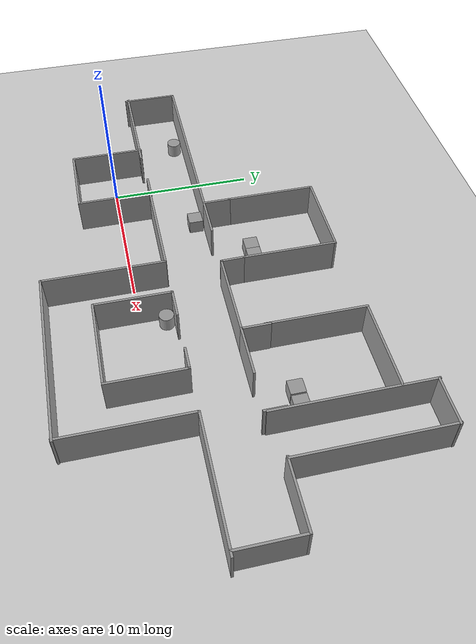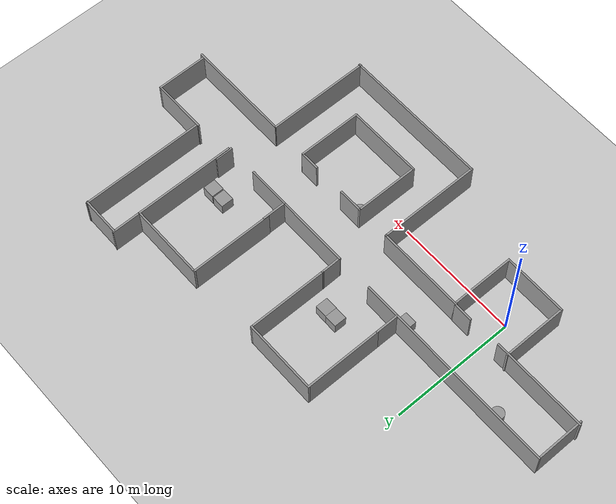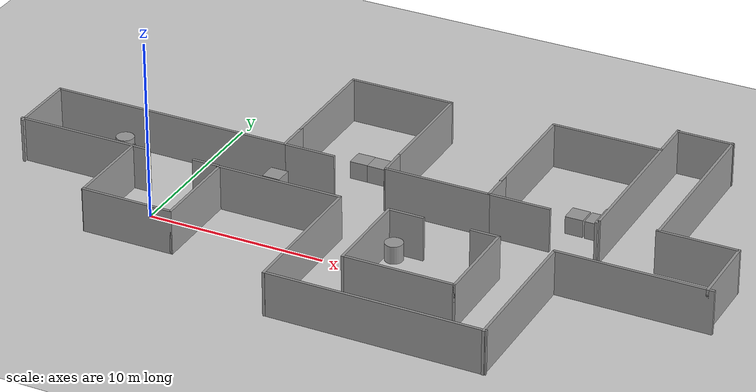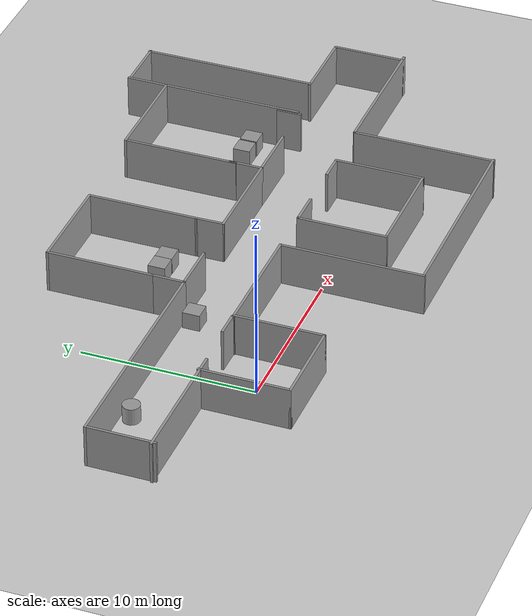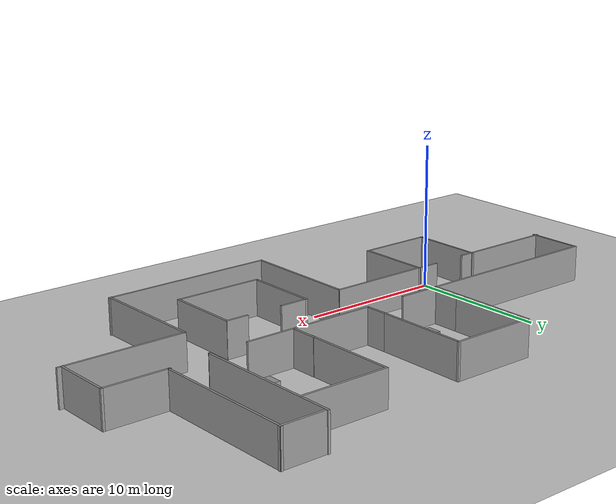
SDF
<sdf version="1.7">
 <world name="default">
  <light name="sun" type="directional">
   <pose>0 0 10 0 -0 0</pose>
   <diffuse>0.8 0.8 0.8 1</diffuse>
   <specular>0.2 0.2 0.2 1</specular>
   <attenuation>
    <range>1000</range>
    <constant>0.9</constant>
    <linear>0.01</linear>
    <quadratic>0.001</quadratic>
   </attenuation>
   <direction>-0.5 0.1 -0.9</direction>
   <spot><inner_angle>0</inner_angle><outer_angle>0</outer_angle><falloff>0</falloff></spot>
  </light>
  <model name="ground_plane">
   <static>1</static>
   <link name="link">
    <collision name="collision">
     <geometry><plane><normal>0 0 1</normal><size>100 100</size></plane></geometry>
     <surface><friction><ode><mu>100</mu><mu2>50</mu2></ode></friction></surface>
    </collision>
    <visual name="visual">
     <cast_shadows>0</cast_shadows>
     <geometry><plane><normal>0 0 1</normal><size>100 100</size></plane></geometry>
     <material>
      <script><uri>file://media/materials/scripts/gazebo.material</uri><name>Gazebo/Grey</name></script>
     </material>
    </visual>
   </link>
  </model>
  <gravity>0 0 -9.8</gravity>
  <magnetic_field>6e-06 2.3e-05 -4.2e-05</magnetic_field>
  <atmosphere type="adiabatic"/>
  <physics type="ode">
   <max_step_size>0.001</max_step_size>
   <real_time_factor>1</real_time_factor>
   <real_time_update_rate>1000</real_time_update_rate>
  </physics>
  <scene><ambient>0.4 0.4 0.4 1</ambient><background>0.7 0.7 0.7 1</background><shadows>1</shadows></scene>
  <spherical_coordinates>
   <surface_model>EARTH_WGS84</surface_model>
   <latitude_deg>0</latitude_deg>
   <longitude_deg>0</longitude_deg>
   <elevation>0</elevation>
   <heading_deg>0</heading_deg>
  </spherical_coordinates>
  <model name="clutter_env023">
   <link name="Wall_0">
    <pose>-12.775 -5.9 0 0 0 -1.5708</pose>
    <visual name="Wall_0_Visual">
     <pose>0 0 1.25 0 -0 0</pose>
     <geometry><box><size>5.25 0.15 2.5</size></box></geometry>
     <material>
      <script><uri>file://media/materials/scripts/gazebo.material</uri><name>Gazebo/Grey</name></script>
      <ambient>1 1 1 1</ambient>
      <shader type="pixel"/>
     </material>
     <meta><layer>0</layer></meta>
    </visual>
    <collision name="Wall_0_Collision">
     <pose>0 0 1.25 0 -0 0</pose>
     <geometry><box><size>5.25 0.15 2.5</size></box></geometry>
     <surface>
      <friction>
       <ode><mu>1</mu><mu2>1</mu2><fdir1>0 0 0</fdir1><slip1>0</slip1><slip2>0</slip2></ode>
       <torsional>
        <coefficient>1</coefficient>
        <patch_radius>0</patch_radius>
        <surface_radius>0</surface_radius>
        <use_patch_radius>1</use_patch_radius>
        <ode><slip>0</slip></ode>
       </torsional>
      </friction>
      <bounce><restitution_coefficient>0</restitution_coefficient><threshold>1e+06</threshold></bounce>
      <contact>
       <collide_without_contact>0</collide_without_contact>
       <collide_without_contact_bitmask>1</collide_without_contact_bitmask>
       <collide_bitmask>1</collide_bitmask>
       <ode>
        <soft_cfm>0</soft_cfm>
        <soft_erp>0.2</soft_erp>
        <kp>1e+13</kp>
        <kd>1</kd>
        <max_vel>0.01</max_vel>
        <min_depth>0</min_depth>
       </ode>
       <bullet>
        <split_impulse>1</split_impulse>
        <split_impulse_penetration_threshold>-0.01</split_impulse_penetration_threshold>
        <soft_cfm>0</soft_cfm>
        <soft_erp>0.2</soft_erp>
        <kp>1e+13</kp>
        <kd>1</kd>
       </bullet>
      </contact>
     </surface>
    </collision>
   </link>
   <link name="Wall_1">
    <pose>-10.225 -8.45 0 0 -0 0</pose>
    <visual name="Wall_1_Visual">
     <pose>0 0 1.25 0 -0 0</pose>
     <geometry><box><size>5.25 0.15 2.5</size></box></geometry>
     <material>
      <script><uri>file://media/materials/scripts/gazebo.material</uri><name>Gazebo/Grey</name></script>
      <ambient>1 1 1 1</ambient>
      <shader type="pixel"/>
     </material>
     <meta><layer>0</layer></meta>
    </visual>
    <collision name="Wall_1_Collision">
     <pose>0 0 1.25 0 -0 0</pose>
     <geometry><box><size>5.25 0.15 2.5</size></box></geometry>
     <surface>
      <friction>
       <ode><mu>1</mu><mu2>1</mu2><fdir1>0 0 0</fdir1><slip1>0</slip1><slip2>0</slip2></ode>
       <torsional>
        <coefficient>1</coefficient>
        <patch_radius>0</patch_radius>
        <surface_radius>0</surface_radius>
        <use_patch_radius>1</use_patch_radius>
        <ode><slip>0</slip></ode>
       </torsional>
      </friction>
      <bounce><restitution_coefficient>0</restitution_coefficient><threshold>1e+06</threshold></bounce>
      <contact>
       <collide_without_contact>0</collide_without_contact>
       <collide_without_contact_bitmask>1</collide_without_contact_bitmask>
       <collide_bitmask>1</collide_bitmask>
       <ode>
        <soft_cfm>0</soft_cfm>
        <soft_erp>0.2</soft_erp>
        <kp>1e+13</kp>
        <kd>1</kd>
        <max_vel>0.01</max_vel>
        <min_depth>0</min_depth>
       </ode>
       <bullet>
        <split_impulse>1</split_impulse>
        <split_impulse_penetration_threshold>-0.01</split_impulse_penetration_threshold>
        <soft_cfm>0</soft_cfm>
        <soft_erp>0.2</soft_erp>
        <kp>1e+13</kp>
        <kd>1</kd>
       </bullet>
      </contact>
     </surface>
    </collision>
   </link>
   <link name="Wall_11">
    <pose>15.101 5.75731 0 0 -0 1.5708</pose>
    <inertial>
     <inertia><ixx>0</ixx><ixy>0</ixy><ixz>0</ixz><iyy>0</iyy><iyz>0</iyz><izz>0</izz></inertia>
     <mass>0</mass>
    </inertial>
    <visual name="Wall_11_Visual">
     <pose>0 0 1.25 0 -0 0</pose>
     <geometry><box><size>10.0758 0.15 2.5</size></box></geometry>
     <material>
      <script><uri>file://media/materials/scripts/gazebo.material</uri><name>Gazebo/Grey</name></script>
      <ambient>1 1 1 1</ambient>
      <shader type="pixel"/>
     </material>
     <meta><layer>0</layer></meta>
    </visual>
    <collision name="Wall_11_Collision">
     <pose>0 0 1.25 0 -0 0</pose>
     <geometry><box><size>10.0758 0.15 2.5</size></box></geometry>
     <surface>
      <friction>
       <ode><mu>1</mu><mu2>1</mu2><fdir1>0 0 0</fdir1><slip1>0</slip1><slip2>0</slip2></ode>
       <torsional>
        <coefficient>1</coefficient>
        <patch_radius>0</patch_radius>
        <surface_radius>0</surface_radius>
        <use_patch_radius>1</use_patch_radius>
        <ode><slip>0</slip></ode>
       </torsional>
      </friction>
      <bounce><restitution_coefficient>0</restitution_coefficient><threshold>1e+06</threshold></bounce>
      <contact>
       <collide_without_contact>0</collide_without_contact>
       <collide_without_contact_bitmask>1</collide_without_contact_bitmask>
       <collide_bitmask>1</collide_bitmask>
       <ode>
        <soft_cfm>0</soft_cfm>
        <soft_erp>0.2</soft_erp>
        <kp>1e+13</kp>
        <kd>1</kd>
        <max_vel>0.01</max_vel>
        <min_depth>0</min_depth>
       </ode>
       <bullet>
        <split_impulse>1</split_impulse>
        <split_impulse_penetration_threshold>-0.01</split_impulse_penetration_threshold>
        <soft_cfm>0</soft_cfm>
        <soft_erp>0.2</soft_erp>
        <kp>1e+13</kp>
        <kd>1</kd>
       </bullet>
      </contact>
     </surface>
    </collision>
   </link>
   <link name="Wall_13">
    <pose>12.0364 5.56961 0 0 -0 1.5708</pose>
    <inertial>
     <inertia><ixx>0</ixx><ixy>0</ixy><ixz>0</ixz><iyy>0</iyy><iyz>0</iyz><izz>0</izz></inertia>
     <mass>0</mass>
    </inertial>
    <visual name="Wall_13_Visual">
     <pose>0 0 1.25 0 -0 0</pose>
     <geometry><box><size>10.4977 0.15 2.5</size></box></geometry>
     <material>
      <script><uri>file://media/materials/scripts/gazebo.material</uri><name>Gazebo/Grey</name></script>
      <ambient>1 1 1 1</ambient>
      <shader type="pixel"/>
     </material>
     <meta><layer>0</layer></meta>
    </visual>
    <collision name="Wall_13_Collision">
     <pose>0 0 1.25 0 -0 0</pose>
     <geometry><box><size>10.4977 0.15 2.5</size></box></geometry>
     <surface>
      <friction>
       <ode><mu>1</mu><mu2>1</mu2><fdir1>0 0 0</fdir1><slip1>0</slip1><slip2>0</slip2></ode>
       <torsional>
        <coefficient>1</coefficient>
        <patch_radius>0</patch_radius>
        <surface_radius>0</surface_radius>
        <use_patch_radius>1</use_patch_radius>
        <ode><slip>0</slip></ode>
       </torsional>
      </friction>
      <bounce><restitution_coefficient>0</restitution_coefficient><threshold>1e+06</threshold></bounce>
      <contact>
       <collide_without_contact>0</collide_without_contact>
       <collide_without_contact_bitmask>1</collide_without_contact_bitmask>
       <collide_bitmask>1</collide_bitmask>
       <ode>
        <soft_cfm>0</soft_cfm>
        <soft_erp>0.2</soft_erp>
        <kp>1e+13</kp>
        <kd>1</kd>
        <max_vel>0.01</max_vel>
        <min_depth>0</min_depth>
       </ode>
       <bullet>
        <split_impulse>1</split_impulse>
        <split_impulse_penetration_threshold>-0.01</split_impulse_penetration_threshold>
        <soft_cfm>0</soft_cfm>
        <soft_erp>0.2</soft_erp>
        <kp>1e+13</kp>
        <kd>1</kd>
       </bullet>
      </contact>
     </surface>
    </collision>
   </link>
   <link name="Wall_14">
    <pose>8.975 8.45 0 0 -0 3.14159</pose>
    <visual name="Wall_14_Visual">
     <pose>0 0 1.25 0 -0 0</pose>
     <geometry><box><size>6.25 0.15 2.5</size></box></geometry>
     <material>
      <script><uri>file://media/materials/scripts/gazebo.material</uri><name>Gazebo/Grey</name></script>
      <ambient>1 1 1 1</ambient>
      <shader type="pixel"/>
     </material>
     <meta><layer>0</layer></meta>
    </visual>
    <collision name="Wall_14_Collision">
     <pose>0 0 1.25 0 -0 0</pose>
     <geometry><box><size>6.25 0.15 2.5</size></box></geometry>
     <surface>
      <friction>
       <ode><mu>1</mu><mu2>1</mu2><fdir1>0 0 0</fdir1><slip1>0</slip1><slip2>0</slip2></ode>
       <torsional>
        <coefficient>1</coefficient>
        <patch_radius>0</patch_radius>
        <surface_radius>0</surface_radius>
        <use_patch_radius>1</use_patch_radius>
        <ode><slip>0</slip></ode>
       </torsional>
      </friction>
      <bounce><restitution_coefficient>0</restitution_coefficient><threshold>1e+06</threshold></bounce>
      <contact>
       <collide_without_contact>0</collide_without_contact>
       <collide_without_contact_bitmask>1</collide_without_contact_bitmask>
       <collide_bitmask>1</collide_bitmask>
       <ode>
        <soft_cfm>0</soft_cfm>
        <soft_erp>0.2</soft_erp>
        <kp>1e+13</kp>
        <kd>1</kd>
        <max_vel>0.01</max_vel>
        <min_depth>0</min_depth>
       </ode>
       <bullet>
        <split_impulse>1</split_impulse>
        <split_impulse_penetration_threshold>-0.01</split_impulse_penetration_threshold>
        <soft_cfm>0</soft_cfm>
        <soft_erp>0.2</soft_erp>
        <kp>1e+13</kp>
        <kd>1</kd>
       </bullet>
      </contact>
     </surface>
    </collision>
   </link>
   <link name="Wall_15">
    <pose>5.925 5.15 0 0 0 -1.5708</pose>
    <visual name="Wall_15_Visual">
     <pose>0 0 1.25 0 -0 0</pose>
     <geometry><box><size>6.75 0.15 2.5</size></box></geometry>
     <material>
      <script><uri>file://media/materials/scripts/gazebo.material</uri><name>Gazebo/Grey</name></script>
      <ambient>1 1 1 1</ambient>
      <shader type="pixel"/>
     </material>
     <meta><layer>0</layer></meta>
    </visual>
    <collision name="Wall_15_Collision">
     <pose>0 0 1.25 0 -0 0</pose>
     <geometry><box><size>6.75 0.15 2.5</size></box></geometry>
     <surface>
      <friction>
       <ode><mu>1</mu><mu2>1</mu2><fdir1>0 0 0</fdir1><slip1>0</slip1><slip2>0</slip2></ode>
       <torsional>
        <coefficient>1</coefficient>
        <patch_radius>0</patch_radius>
        <surface_radius>0</surface_radius>
        <use_patch_radius>1</use_patch_radius>
        <ode><slip>0</slip></ode>
       </torsional>
      </friction>
      <bounce><restitution_coefficient>0</restitution_coefficient><threshold>1e+06</threshold></bounce>
      <contact>
       <collide_without_contact>0</collide_without_contact>
       <collide_without_contact_bitmask>1</collide_without_contact_bitmask>
       <collide_bitmask>1</collide_bitmask>
       <ode>
        <soft_cfm>0</soft_cfm>
        <soft_erp>0.2</soft_erp>
        <kp>1e+13</kp>
        <kd>1</kd>
        <max_vel>0.01</max_vel>
        <min_depth>0</min_depth>
       </ode>
       <bullet>
        <split_impulse>1</split_impulse>
        <split_impulse_penetration_threshold>-0.01</split_impulse_penetration_threshold>
        <soft_cfm>0</soft_cfm>
        <soft_erp>0.2</soft_erp>
        <kp>1e+13</kp>
        <kd>1</kd>
       </bullet>
      </contact>
     </surface>
    </collision>
   </link>
   <link name="Wall_17">
    <pose>0.074999 5.025 0 0 -0 1.5708</pose>
    <visual name="Wall_17_Visual">
     <pose>0 0 1.25 0 -0 0</pose>
     <geometry><box><size>6.5 0.15 2.5</size></box></geometry>
     <material>
      <script><uri>file://media/materials/scripts/gazebo.material</uri><name>Gazebo/Grey</name></script>
      <ambient>1 1 1 1</ambient>
      <shader type="pixel"/>
     </material>
     <meta><layer>0</layer></meta>
    </visual>
    <collision name="Wall_17_Collision">
     <pose>0 0 1.25 0 -0 0</pose>
     <geometry><box><size>6.5 0.15 2.5</size></box></geometry>
     <surface>
      <friction>
       <ode><mu>1</mu><mu2>1</mu2><fdir1>0 0 0</fdir1><slip1>0</slip1><slip2>0</slip2></ode>
       <torsional>
        <coefficient>1</coefficient>
        <patch_radius>0</patch_radius>
        <surface_radius>0</surface_radius>
        <use_patch_radius>1</use_patch_radius>
        <ode><slip>0</slip></ode>
       </torsional>
      </friction>
      <bounce><restitution_coefficient>0</restitution_coefficient><threshold>1e+06</threshold></bounce>
      <contact>
       <collide_without_contact>0</collide_without_contact>
       <collide_without_contact_bitmask>1</collide_without_contact_bitmask>
       <collide_bitmask>1</collide_bitmask>
       <ode>
        <soft_cfm>0</soft_cfm>
        <soft_erp>0.2</soft_erp>
        <kp>1e+13</kp>
        <kd>1</kd>
        <max_vel>0.01</max_vel>
        <min_depth>0</min_depth>
       </ode>
       <bullet>
        <split_impulse>1</split_impulse>
        <split_impulse_penetration_threshold>-0.01</split_impulse_penetration_threshold>
        <soft_cfm>0</soft_cfm>
        <soft_erp>0.2</soft_erp>
        <kp>1e+13</kp>
        <kd>1</kd>
       </bullet>
      </contact>
     </surface>
    </collision>
   </link>
   <link name="Wall_18">
    <pose>-2.85 8.2 0 0 -0 3.14159</pose>
    <visual name="Wall_18_Visual">
     <pose>0 0 1.25 0 -0 0</pose>
     <geometry><box><size>6 0.15 2.5</size></box></geometry>
     <material>
      <script><uri>file://media/materials/scripts/gazebo.material</uri><name>Gazebo/Grey</name></script>
      <ambient>1 1 1 1</ambient>
      <shader type="pixel"/>
     </material>
     <meta><layer>0</layer></meta>
    </visual>
    <collision name="Wall_18_Collision">
     <pose>0 0 1.25 0 -0 0</pose>
     <geometry><box><size>6 0.15 2.5</size></box></geometry>
     <surface>
      <friction>
       <ode><mu>1</mu><mu2>1</mu2><fdir1>0 0 0</fdir1><slip1>0</slip1><slip2>0</slip2></ode>
       <torsional>
        <coefficient>1</coefficient>
        <patch_radius>0</patch_radius>
        <surface_radius>0</surface_radius>
        <use_patch_radius>1</use_patch_radius>
        <ode><slip>0</slip></ode>
       </torsional>
      </friction>
      <bounce><restitution_coefficient>0</restitution_coefficient><threshold>1e+06</threshold></bounce>
      <contact>
       <collide_without_contact>0</collide_without_contact>
       <collide_without_contact_bitmask>1</collide_without_contact_bitmask>
       <collide_bitmask>1</collide_bitmask>
       <ode>
        <soft_cfm>0</soft_cfm>
        <soft_erp>0.2</soft_erp>
        <kp>1e+13</kp>
        <kd>1</kd>
        <max_vel>0.01</max_vel>
        <min_depth>0</min_depth>
       </ode>
       <bullet>
        <split_impulse>1</split_impulse>
        <split_impulse_penetration_threshold>-0.01</split_impulse_penetration_threshold>
        <soft_cfm>0</soft_cfm>
        <soft_erp>0.2</soft_erp>
        <kp>1e+13</kp>
        <kd>1</kd>
       </bullet>
      </contact>
     </surface>
    </collision>
   </link>
   <link name="Wall_19">
    <pose>-5.775 5.15 0 0 0 -1.5708</pose>
    <visual name="Wall_19_Visual">
     <pose>0 0 1.25 0 -0 0</pose>
     <geometry><box><size>6.25 0.15 2.5</size></box></geometry>
     <material>
      <script><uri>file://media/materials/scripts/gazebo.material</uri><name>Gazebo/Grey</name></script>
      <ambient>1 1 1 1</ambient>
      <shader type="pixel"/>
     </material>
     <meta><layer>0</layer></meta>
    </visual>
    <collision name="Wall_19_Collision">
     <pose>0 0 1.25 0 -0 0</pose>
     <geometry><box><size>6.25 0.15 2.5</size></box></geometry>
     <surface>
      <friction>
       <ode><mu>1</mu><mu2>1</mu2><fdir1>0 0 0</fdir1><slip1>0</slip1><slip2>0</slip2></ode>
       <torsional>
        <coefficient>1</coefficient>
        <patch_radius>0</patch_radius>
        <surface_radius>0</surface_radius>
        <use_patch_radius>1</use_patch_radius>
        <ode><slip>0</slip></ode>
       </torsional>
      </friction>
      <bounce><restitution_coefficient>0</restitution_coefficient><threshold>1e+06</threshold></bounce>
      <contact>
       <collide_without_contact>0</collide_without_contact>
       <collide_without_contact_bitmask>1</collide_without_contact_bitmask>
       <collide_bitmask>1</collide_bitmask>
       <ode>
        <soft_cfm>0</soft_cfm>
        <soft_erp>0.2</soft_erp>
        <kp>1e+13</kp>
        <kd>1</kd>
        <max_vel>0.01</max_vel>
        <min_depth>0</min_depth>
       </ode>
       <bullet>
        <split_impulse>1</split_impulse>
        <split_impulse_penetration_threshold>-0.01</split_impulse_penetration_threshold>
        <soft_cfm>0</soft_cfm>
        <soft_erp>0.2</soft_erp>
        <kp>1e+13</kp>
        <kd>1</kd>
       </bullet>
      </contact>
     </surface>
    </collision>
   </link>
   <link name="Wall_2">
    <pose>-7.675 -5.9 0 0 -0 1.5708</pose>
    <visual name="Wall_2_Visual">
     <pose>0 0 1.25 0 -0 0</pose>
     <geometry><box><size>5.25 0.15 2.5</size></box></geometry>
     <material>
      <script><uri>file://media/materials/scripts/gazebo.material</uri><name>Gazebo/Grey</name></script>
      <ambient>1 1 1 1</ambient>
      <shader type="pixel"/>
     </material>
     <meta><layer>0</layer></meta>
    </visual>
    <collision name="Wall_2_Collision">
     <pose>0 0 1.25 0 -0 0</pose>
     <geometry><box><size>5.25 0.15 2.5</size></box></geometry>
     <surface>
      <friction>
       <ode><mu>1</mu><mu2>1</mu2><fdir1>0 0 0</fdir1><slip1>0</slip1><slip2>0</slip2></ode>
       <torsional>
        <coefficient>1</coefficient>
        <patch_radius>0</patch_radius>
        <surface_radius>0</surface_radius>
        <use_patch_radius>1</use_patch_radius>
        <ode><slip>0</slip></ode>
       </torsional>
      </friction>
      <bounce><restitution_coefficient>0</restitution_coefficient><threshold>1e+06</threshold></bounce>
      <contact>
       <collide_without_contact>0</collide_without_contact>
       <collide_without_contact_bitmask>1</collide_without_contact_bitmask>
       <collide_bitmask>1</collide_bitmask>
       <ode>
        <soft_cfm>0</soft_cfm>
        <soft_erp>0.2</soft_erp>
        <kp>1e+13</kp>
        <kd>1</kd>
        <max_vel>0.01</max_vel>
        <min_depth>0</min_depth>
       </ode>
       <bullet>
        <split_impulse>1</split_impulse>
        <split_impulse_penetration_threshold>-0.01</split_impulse_penetration_threshold>
        <soft_cfm>0</soft_cfm>
        <soft_erp>0.2</soft_erp>
        <kp>1e+13</kp>
        <kd>1</kd>
       </bullet>
      </contact>
     </surface>
    </collision>
   </link>
   <link name="Wall_20">
    <pose>-5.775 1.175 0 0 0 -1.5708</pose>
    <visual name="Wall_20_Visual">
     <pose>0 0 1.25 0 -0 0</pose>
     <geometry><box><size>2 0.15 2.5</size></box></geometry>
     <material>
      <script><uri>file://media/materials/scripts/gazebo.material</uri><name>Gazebo/Grey</name></script>
      <ambient>1 1 1 1</ambient>
      <shader type="pixel"/>
     </material>
     <meta><layer>0</layer></meta>
    </visual>
    <collision name="Wall_20_Collision">
     <pose>0 0 1.25 0 -0 0</pose>
     <geometry><box><size>2 0.15 2.5</size></box></geometry>
     <surface>
      <friction>
       <ode><mu>1</mu><mu2>1</mu2><fdir1>0 0 0</fdir1><slip1>0</slip1><slip2>0</slip2></ode>
       <torsional>
        <coefficient>1</coefficient>
        <patch_radius>0</patch_radius>
        <surface_radius>0</surface_radius>
        <use_patch_radius>1</use_patch_radius>
        <ode><slip>0</slip></ode>
       </torsional>
      </friction>
      <bounce><restitution_coefficient>0</restitution_coefficient><threshold>1e+06</threshold></bounce>
      <contact>
       <collide_without_contact>0</collide_without_contact>
       <collide_without_contact_bitmask>1</collide_without_contact_bitmask>
       <collide_bitmask>1</collide_bitmask>
       <ode>
        <soft_cfm>0</soft_cfm>
        <soft_erp>0.2</soft_erp>
        <kp>1e+13</kp>
        <kd>1</kd>
        <max_vel>0.01</max_vel>
        <min_depth>0</min_depth>
       </ode>
       <bullet>
        <split_impulse>1</split_impulse>
        <split_impulse_penetration_threshold>-0.01</split_impulse_penetration_threshold>
        <soft_cfm>0</soft_cfm>
        <soft_erp>0.2</soft_erp>
        <kp>1e+13</kp>
        <kd>1</kd>
       </bullet>
      </contact>
     </surface>
    </collision>
   </link>
   <link name="Wall_21">
    <pose>-12.575 0.25 0 0 -0 3.14159</pose>
    <visual name="Wall_21_Visual">
     <pose>0 0 1.25 0 -0 0</pose>
     <geometry><box><size>13.75 0.15 2.5</size></box></geometry>
     <material>
      <script><uri>file://media/materials/scripts/gazebo.material</uri><name>Gazebo/Grey</name></script>
      <ambient>1 1 1 1</ambient>
      <shader type="pixel"/>
     </material>
     <meta><layer>0</layer></meta>
    </visual>
    <collision name="Wall_21_Collision">
     <pose>0 0 1.25 0 -0 0</pose>
     <geometry><box><size>13.75 0.15 2.5</size></box></geometry>
     <surface>
      <friction>
       <ode><mu>1</mu><mu2>1</mu2><fdir1>0 0 0</fdir1><slip1>0</slip1><slip2>0</slip2></ode>
       <torsional>
        <coefficient>1</coefficient>
        <patch_radius>0</patch_radius>
        <surface_radius>0</surface_radius>
        <use_patch_radius>1</use_patch_radius>
        <ode><slip>0</slip></ode>
       </torsional>
      </friction>
      <bounce><restitution_coefficient>0</restitution_coefficient><threshold>1e+06</threshold></bounce>
      <contact>
       <collide_without_contact>0</collide_without_contact>
       <collide_without_contact_bitmask>1</collide_without_contact_bitmask>
       <collide_bitmask>1</collide_bitmask>
       <ode>
        <soft_cfm>0</soft_cfm>
        <soft_erp>0.2</soft_erp>
        <kp>1e+13</kp>
        <kd>1</kd>
        <max_vel>0.01</max_vel>
        <min_depth>0</min_depth>
       </ode>
       <bullet>
        <split_impulse>1</split_impulse>
        <split_impulse_penetration_threshold>-0.01</split_impulse_penetration_threshold>
        <soft_cfm>0</soft_cfm>
        <soft_erp>0.2</soft_erp>
        <kp>1e+13</kp>
        <kd>1</kd>
       </bullet>
      </contact>
     </surface>
    </collision>
   </link>
   <link name="Wall_22">
    <pose>-19.375 -1.675 0 0 0 -1.5708</pose>
    <visual name="Wall_22_Visual">
     <pose>0 0 1.25 0 -0 0</pose>
     <geometry><box><size>4 0.15 2.5</size></box></geometry>
     <material>
      <script><uri>file://media/materials/scripts/gazebo.material</uri><name>Gazebo/Grey</name></script>
      <ambient>1 1 1 1</ambient>
      <shader type="pixel"/>
     </material>
     <meta><layer>0</layer></meta>
    </visual>
    <collision name="Wall_22_Collision">
     <pose>0 0 1.25 0 -0 0</pose>
     <geometry><box><size>4 0.15 2.5</size></box></geometry>
     <surface>
      <friction>
       <ode><mu>1</mu><mu2>1</mu2><fdir1>0 0 0</fdir1><slip1>0</slip1><slip2>0</slip2></ode>
       <torsional>
        <coefficient>1</coefficient>
        <patch_radius>0</patch_radius>
        <surface_radius>0</surface_radius>
        <use_patch_radius>1</use_patch_radius>
        <ode><slip>0</slip></ode>
       </torsional>
      </friction>
      <bounce><restitution_coefficient>0</restitution_coefficient><threshold>1e+06</threshold></bounce>
      <contact>
       <collide_without_contact>0</collide_without_contact>
       <collide_without_contact_bitmask>1</collide_without_contact_bitmask>
       <collide_bitmask>1</collide_bitmask>
       <ode>
        <soft_cfm>0</soft_cfm>
        <soft_erp>0.2</soft_erp>
        <kp>1e+13</kp>
        <kd>1</kd>
        <max_vel>0.01</max_vel>
        <min_depth>0</min_depth>
       </ode>
       <bullet>
        <split_impulse>1</split_impulse>
        <split_impulse_penetration_threshold>-0.01</split_impulse_penetration_threshold>
        <soft_cfm>0</soft_cfm>
        <soft_erp>0.2</soft_erp>
        <kp>1e+13</kp>
        <kd>1</kd>
       </bullet>
      </contact>
     </surface>
    </collision>
   </link>
   <link name="Wall_23">
    <pose>-15.6606 -3.42681 0 0 -0 0</pose>
    <inertial>
     <inertia><ixx>0</ixx><ixy>0</ixy><ixz>0</ixz><iyy>0</iyy><iyz>0</iyz><izz>0</izz></inertia>
     <mass>0</mass>
    </inertial>
    <visual name="Wall_23_Visual">
     <pose>0 0 1.25 0 -0 0</pose>
     <geometry><box><size>7.79202 0.15 2.5</size></box></geometry>
     <material>
      <script><uri>file://media/materials/scripts/gazebo.material</uri><name>Gazebo/Grey</name></script>
      <ambient>1 1 1 1</ambient>
      <shader type="pixel"/>
     </material>
     <meta><layer>0</layer></meta>
    </visual>
    <collision name="Wall_23_Collision">
     <pose>0 0 1.25 0 -0 0</pose>
     <geometry><box><size>7.79202 0.15 2.5</size></box></geometry>
     <surface>
      <friction>
       <ode><mu>1</mu><mu2>1</mu2><fdir1>0 0 0</fdir1><slip1>0</slip1><slip2>0</slip2></ode>
       <torsional>
        <coefficient>1</coefficient>
        <patch_radius>0</patch_radius>
        <surface_radius>0</surface_radius>
        <use_patch_radius>1</use_patch_radius>
        <ode><slip>0</slip></ode>
       </torsional>
      </friction>
      <bounce><restitution_coefficient>0</restitution_coefficient><threshold>1e+06</threshold></bounce>
      <contact>
       <collide_without_contact>0</collide_without_contact>
       <collide_without_contact_bitmask>1</collide_without_contact_bitmask>
       <collide_bitmask>1</collide_bitmask>
       <ode>
        <soft_cfm>0</soft_cfm>
        <soft_erp>0.2</soft_erp>
        <kp>1e+13</kp>
        <kd>1</kd>
        <max_vel>0.01</max_vel>
        <min_depth>0</min_depth>
       </ode>
       <bullet>
        <split_impulse>1</split_impulse>
        <split_impulse_penetration_threshold>-0.01</split_impulse_penetration_threshold>
        <soft_cfm>0</soft_cfm>
        <soft_erp>0.2</soft_erp>
        <kp>1e+13</kp>
        <kd>1</kd>
       </bullet>
      </contact>
     </surface>
    </collision>
   </link>
   <link name="Wall_25">
    <pose>-4.35 0.25 0 0 -0 0</pose>
    <visual name="Wall_25_Visual">
     <pose>0 0 1.25 0 -0 0</pose>
     <geometry><box><size>3 0.15 2.5</size></box></geometry>
     <material>
      <script><uri>file://media/materials/scripts/gazebo.material</uri><name>Gazebo/Grey</name></script>
      <ambient>1 1 1 1</ambient>
      <shader type="pixel"/>
     </material>
     <meta><layer>0</layer></meta>
    </visual>
    <collision name="Wall_25_Collision">
     <pose>0 0 1.25 0 -0 0</pose>
     <geometry><box><size>3 0.15 2.5</size></box></geometry>
     <surface>
      <friction>
       <ode><mu>1</mu><mu2>1</mu2><fdir1>0 0 0</fdir1><slip1>0</slip1><slip2>0</slip2></ode>
       <torsional>
        <coefficient>1</coefficient>
        <patch_radius>0</patch_radius>
        <surface_radius>0</surface_radius>
        <use_patch_radius>1</use_patch_radius>
        <ode><slip>0</slip></ode>
       </torsional>
      </friction>
      <bounce><restitution_coefficient>0</restitution_coefficient><threshold>1e+06</threshold></bounce>
      <contact>
       <collide_without_contact>0</collide_without_contact>
       <collide_without_contact_bitmask>1</collide_without_contact_bitmask>
       <collide_bitmask>1</collide_bitmask>
       <ode>
        <soft_cfm>0</soft_cfm>
        <soft_erp>0.2</soft_erp>
        <kp>1e+13</kp>
        <kd>1</kd>
        <max_vel>0.01</max_vel>
        <min_depth>0</min_depth>
       </ode>
       <bullet>
        <split_impulse>1</split_impulse>
        <split_impulse_penetration_threshold>-0.01</split_impulse_penetration_threshold>
        <soft_cfm>0</soft_cfm>
        <soft_erp>0.2</soft_erp>
        <kp>1e+13</kp>
        <kd>1</kd>
       </bullet>
      </contact>
     </surface>
    </collision>
   </link>
   <link name="Wall_27">
    <pose>3.03081 0.283447 0 0 -0 0</pose>
    <visual name="Wall_27_Visual">
     <pose>0 0 1.25 0 -0 0</pose>
     <geometry><box><size>6 0.15 2.5</size></box></geometry>
     <material>
      <script><uri>file://media/materials/scripts/gazebo.material</uri><name>Gazebo/Grey</name></script>
      <ambient>1 1 1 1</ambient>
      <shader type="pixel"/>
     </material>
     <meta><layer>0</layer></meta>
    </visual>
    <collision name="Wall_27_Collision">
     <pose>0 0 1.25 0 -0 0</pose>
     <geometry><box><size>6 0.15 2.5</size></box></geometry>
     <surface>
      <friction>
       <ode><mu>1</mu><mu2>1</mu2><fdir1>0 0 0</fdir1><slip1>0</slip1><slip2>0</slip2></ode>
       <torsional>
        <coefficient>1</coefficient>
        <patch_radius>0</patch_radius>
        <surface_radius>0</surface_radius>
        <use_patch_radius>1</use_patch_radius>
        <ode><slip>0</slip></ode>
       </torsional>
      </friction>
      <bounce><restitution_coefficient>0</restitution_coefficient><threshold>1e+06</threshold></bounce>
      <contact>
       <collide_without_contact>0</collide_without_contact>
       <collide_without_contact_bitmask>1</collide_without_contact_bitmask>
       <collide_bitmask>1</collide_bitmask>
       <ode>
        <soft_cfm>0</soft_cfm>
        <soft_erp>0.2</soft_erp>
        <kp>1e+13</kp>
        <kd>1</kd>
        <max_vel>0.01</max_vel>
        <min_depth>0</min_depth>
       </ode>
       <bullet>
        <split_impulse>1</split_impulse>
        <split_impulse_penetration_threshold>-0.01</split_impulse_penetration_threshold>
        <soft_cfm>0</soft_cfm>
        <soft_erp>0.2</soft_erp>
        <kp>1e+13</kp>
        <kd>1</kd>
       </bullet>
      </contact>
     </surface>
    </collision>
   </link>
   <link name="Wall_28">
    <pose>5.95581 1.20845 0 0 -0 1.5708</pose>
    <visual name="Wall_28_Visual">
     <pose>0 0 1.25 0 -0 0</pose>
     <geometry><box><size>2 0.15 2.5</size></box></geometry>
     <material>
      <script><uri>file://media/materials/scripts/gazebo.material</uri><name>Gazebo/Grey</name></script>
      <ambient>1 1 1 1</ambient>
      <shader type="pixel"/>
     </material>
     <meta><layer>0</layer></meta>
    </visual>
    <collision name="Wall_28_Collision">
     <pose>0 0 1.25 0 -0 0</pose>
     <geometry><box><size>2 0.15 2.5</size></box></geometry>
     <surface>
      <friction>
       <ode><mu>1</mu><mu2>1</mu2><fdir1>0 0 0</fdir1><slip1>0</slip1><slip2>0</slip2></ode>
       <torsional>
        <coefficient>1</coefficient>
        <patch_radius>0</patch_radius>
        <surface_radius>0</surface_radius>
        <use_patch_radius>1</use_patch_radius>
        <ode><slip>0</slip></ode>
       </torsional>
      </friction>
      <bounce><restitution_coefficient>0</restitution_coefficient><threshold>1e+06</threshold></bounce>
      <contact>
       <collide_without_contact>0</collide_without_contact>
       <collide_without_contact_bitmask>1</collide_without_contact_bitmask>
       <collide_bitmask>1</collide_bitmask>
       <ode>
        <soft_cfm>0</soft_cfm>
        <soft_erp>0.2</soft_erp>
        <kp>1e+13</kp>
        <kd>1</kd>
        <max_vel>0.01</max_vel>
        <min_depth>0</min_depth>
       </ode>
       <bullet>
        <split_impulse>1</split_impulse>
        <split_impulse_penetration_threshold>-0.01</split_impulse_penetration_threshold>
        <soft_cfm>0</soft_cfm>
        <soft_erp>0.2</soft_erp>
        <kp>1e+13</kp>
        <kd>1</kd>
       </bullet>
      </contact>
     </surface>
    </collision>
   </link>
   <link name="Wall_2_clone_0">
    <pose>-0.68287 -7.47635 0 0 -0 1.5708</pose>
    <inertial>
     <inertia><ixx>0</ixx><ixy>0</ixy><ixz>0</ixz><iyy>0</iyy><iyz>0</iyz><izz>0</izz></inertia>
     <mass>0</mass>
    </inertial>
    <visual name="Wall_2_Visual">
     <pose>0 0 1.25 0 -0 0</pose>
     <geometry><box><size>8.33804 0.15 2.5</size></box></geometry>
     <material>
      <script><uri>file://media/materials/scripts/gazebo.material</uri><name>Gazebo/Grey</name></script>
      <ambient>1 1 1 1</ambient>
      <shader type="pixel"/>
     </material>
     <meta><layer>0</layer></meta>
    </visual>
    <collision name="Wall_2_Collision">
     <pose>0 0 1.25 0 -0 0</pose>
     <geometry><box><size>8.33804 0.15 2.5</size></box></geometry>
     <surface>
      <friction>
       <ode><mu>1</mu><mu2>1</mu2><fdir1>0 0 0</fdir1><slip1>0</slip1><slip2>0</slip2></ode>
       <torsional>
        <coefficient>1</coefficient>
        <patch_radius>0</patch_radius>
        <surface_radius>0</surface_radius>
        <use_patch_radius>1</use_patch_radius>
        <ode><slip>0</slip></ode>
       </torsional>
      </friction>
      <bounce><restitution_coefficient>0</restitution_coefficient><threshold>1e+06</threshold></bounce>
      <contact>
       <collide_without_contact>0</collide_without_contact>
       <collide_without_contact_bitmask>1</collide_without_contact_bitmask>
       <collide_bitmask>1</collide_bitmask>
       <ode>
        <soft_cfm>0</soft_cfm>
        <soft_erp>0.2</soft_erp>
        <kp>1e+13</kp>
        <kd>1</kd>
        <max_vel>0.01</max_vel>
        <min_depth>0</min_depth>
       </ode>
       <bullet>
        <split_impulse>1</split_impulse>
        <split_impulse_penetration_threshold>-0.01</split_impulse_penetration_threshold>
        <soft_cfm>0</soft_cfm>
        <soft_erp>0.2</soft_erp>
        <kp>1e+13</kp>
        <kd>1</kd>
       </bullet>
      </contact>
     </surface>
    </collision>
   </link>
   <link name="Wall_2_clone_0_clone">
    <pose>11.2085 -7.50081 0 0 -0 1.5708</pose>
    <inertial>
     <inertia><ixx>0</ixx><ixy>0</ixy><ixz>0</ixz><iyy>0</iyy><iyz>0</iyz><izz>0</izz></inertia>
     <mass>0</mass>
    </inertial>
    <visual name="Wall_2_Visual">
     <pose>0 0 1.25 0 -0 0</pose>
     <geometry><box><size>8.33804 0.15 2.5</size></box></geometry>
     <material>
      <script><uri>file://media/materials/scripts/gazebo.material</uri><name>Gazebo/Grey</name></script>
      <ambient>1 1 1 1</ambient>
      <shader type="pixel"/>
     </material>
     <meta><layer>0</layer></meta>
    </visual>
    <collision name="Wall_2_Collision">
     <pose>0 0 1.25 0 -0 0</pose>
     <geometry><box><size>8.33804 0.15 2.5</size></box></geometry>
     <surface>
      <friction>
       <ode><mu>1</mu><mu2>1</mu2><fdir1>0 0 0</fdir1><slip1>0</slip1><slip2>0</slip2></ode>
       <torsional>
        <coefficient>1</coefficient>
        <patch_radius>0</patch_radius>
        <surface_radius>0</surface_radius>
        <use_patch_radius>1</use_patch_radius>
        <ode><slip>0</slip></ode>
       </torsional>
      </friction>
      <bounce><restitution_coefficient>0</restitution_coefficient><threshold>1e+06</threshold></bounce>
      <contact>
       <collide_without_contact>0</collide_without_contact>
       <collide_without_contact_bitmask>1</collide_without_contact_bitmask>
       <collide_bitmask>1</collide_bitmask>
       <ode>
        <soft_cfm>0</soft_cfm>
        <soft_erp>0.2</soft_erp>
        <kp>1e+13</kp>
        <kd>1</kd>
        <max_vel>0.01</max_vel>
        <min_depth>0</min_depth>
       </ode>
       <bullet>
        <split_impulse>1</split_impulse>
        <split_impulse_penetration_threshold>-0.01</split_impulse_penetration_threshold>
        <soft_cfm>0</soft_cfm>
        <soft_erp>0.2</soft_erp>
        <kp>1e+13</kp>
        <kd>1</kd>
       </bullet>
      </contact>
     </surface>
    </collision>
   </link>
   <link name="Wall_3">
    <pose>-8.50057 -3.3019 0 0 -0 3.14159</pose>
    <inertial>
     <inertia><ixx>0</ixx><ixy>0</ixy><ixz>0</ixz><iyy>0</iyy><iyz>0</iyz><izz>0</izz></inertia>
     <mass>0</mass>
    </inertial>
    <visual name="Wall_3_Visual">
     <pose>0 0 1.25 0 -0 0</pose>
     <geometry><box><size>1.54468 0.15 2.5</size></box></geometry>
     <material>
      <script><uri>file://media/materials/scripts/gazebo.material</uri><name>Gazebo/Grey</name></script>
      <ambient>1 1 1 1</ambient>
      <shader type="pixel"/>
     </material>
     <meta><layer>0</layer></meta>
    </visual>
    <collision name="Wall_3_Collision">
     <pose>0 0 1.25 0 -0 0</pose>
     <geometry><box><size>1.54468 0.15 2.5</size></box></geometry>
     <surface>
      <friction>
       <ode><mu>1</mu><mu2>1</mu2><fdir1>0 0 0</fdir1><slip1>0</slip1><slip2>0</slip2></ode>
       <torsional>
        <coefficient>1</coefficient>
        <patch_radius>0</patch_radius>
        <surface_radius>0</surface_radius>
        <use_patch_radius>1</use_patch_radius>
        <ode><slip>0</slip></ode>
       </torsional>
      </friction>
      <bounce><restitution_coefficient>0</restitution_coefficient><threshold>1e+06</threshold></bounce>
      <contact>
       <collide_without_contact>0</collide_without_contact>
       <collide_without_contact_bitmask>1</collide_without_contact_bitmask>
       <collide_bitmask>1</collide_bitmask>
       <ode>
        <soft_cfm>0</soft_cfm>
        <soft_erp>0.2</soft_erp>
        <kp>1e+13</kp>
        <kd>1</kd>
        <max_vel>0.01</max_vel>
        <min_depth>0</min_depth>
       </ode>
       <bullet>
        <split_impulse>1</split_impulse>
        <split_impulse_penetration_threshold>-0.01</split_impulse_penetration_threshold>
        <soft_cfm>0</soft_cfm>
        <soft_erp>0.2</soft_erp>
        <kp>1e+13</kp>
        <kd>1</kd>
       </bullet>
      </contact>
     </surface>
    </collision>
   </link>
   <link name="Wall_30">
    <pose>7.63081 0.283447 0 0 -0 0</pose>
    <visual name="Wall_30_Visual">
     <pose>0 0 1.25 0 -0 0</pose>
     <geometry><box><size>3.5 0.15 2.5</size></box></geometry>
     <material>
      <script><uri>file://media/materials/scripts/gazebo.material</uri><name>Gazebo/Grey</name></script>
      <ambient>1 1 1 1</ambient>
      <shader type="pixel"/>
     </material>
     <meta><layer>0</layer></meta>
    </visual>
    <collision name="Wall_30_Collision">
     <pose>0 0 1.25 0 -0 0</pose>
     <geometry><box><size>3.5 0.15 2.5</size></box></geometry>
     <surface>
      <friction>
       <ode><mu>1</mu><mu2>1</mu2><fdir1>0 0 0</fdir1><slip1>0</slip1><slip2>0</slip2></ode>
       <torsional>
        <coefficient>1</coefficient>
        <patch_radius>0</patch_radius>
        <surface_radius>0</surface_radius>
        <use_patch_radius>1</use_patch_radius>
        <ode><slip>0</slip></ode>
       </torsional>
      </friction>
      <bounce><restitution_coefficient>0</restitution_coefficient><threshold>1e+06</threshold></bounce>
      <contact>
       <collide_without_contact>0</collide_without_contact>
       <collide_without_contact_bitmask>1</collide_without_contact_bitmask>
       <collide_bitmask>1</collide_bitmask>
       <ode>
        <soft_cfm>0</soft_cfm>
        <soft_erp>0.2</soft_erp>
        <kp>1e+13</kp>
        <kd>1</kd>
        <max_vel>0.01</max_vel>
        <min_depth>0</min_depth>
       </ode>
       <bullet>
        <split_impulse>1</split_impulse>
        <split_impulse_penetration_threshold>-0.01</split_impulse_penetration_threshold>
        <soft_cfm>0</soft_cfm>
        <soft_erp>0.2</soft_erp>
        <kp>1e+13</kp>
        <kd>1</kd>
       </bullet>
      </contact>
     </surface>
    </collision>
   </link>
   <link name="Wall_32">
    <pose>0.090406 1.06672 0 0 0 -1.55113</pose>
    <visual name="Wall_32_Visual">
     <pose>0 0 1.25 0 -0 0</pose>
     <geometry><box><size>1.71686 0.15 2.5</size></box></geometry>
     <material>
      <script><uri>file://media/materials/scripts/gazebo.material</uri><name>Gazebo/Grey</name></script>
      <ambient>1 1 1 1</ambient>
      <shader type="pixel"/>
     </material>
     <meta><layer>0</layer></meta>
    </visual>
    <collision name="Wall_32_Collision">
     <pose>0 0 1.25 0 -0 0</pose>
     <geometry><box><size>1.71686 0.15 2.5</size></box></geometry>
     <surface>
      <friction>
       <ode><mu>1</mu><mu2>1</mu2><fdir1>0 0 0</fdir1><slip1>0</slip1><slip2>0</slip2></ode>
       <torsional>
        <coefficient>1</coefficient>
        <patch_radius>0</patch_radius>
        <surface_radius>0</surface_radius>
        <use_patch_radius>1</use_patch_radius>
        <ode><slip>0</slip></ode>
       </torsional>
      </friction>
      <bounce><restitution_coefficient>0</restitution_coefficient><threshold>1e+06</threshold></bounce>
      <contact>
       <collide_without_contact>0</collide_without_contact>
       <collide_without_contact_bitmask>1</collide_without_contact_bitmask>
       <collide_bitmask>1</collide_bitmask>
       <ode>
        <soft_cfm>0</soft_cfm>
        <soft_erp>0.2</soft_erp>
        <kp>1e+13</kp>
        <kd>1</kd>
        <max_vel>0.01</max_vel>
        <min_depth>0</min_depth>
       </ode>
       <bullet>
        <split_impulse>1</split_impulse>
        <split_impulse_penetration_threshold>-0.01</split_impulse_penetration_threshold>
        <soft_cfm>0</soft_cfm>
        <soft_erp>0.2</soft_erp>
        <kp>1e+13</kp>
        <kd>1</kd>
       </bullet>
      </contact>
     </surface>
    </collision>
   </link>
   <link name="Wall_34">
    <pose>3.02588 -3.35097 0 0 -0 0</pose>
    <inertial>
     <inertia><ixx>0</ixx><ixy>0</ixy><ixz>0</ixz><iyy>0</iyy><iyz>0</iyz><izz>0</izz></inertia>
     <mass>0</mass>
    </inertial>
    <visual name="Wall_34_Visual">
     <pose>0 0 1.25 0 -0 0</pose>
     <geometry><box><size>2.04819 0.15 2.5</size></box></geometry>
     <material>
      <script><uri>file://media/materials/scripts/gazebo.material</uri><name>Gazebo/Grey</name></script>
      <ambient>1 1 1 1</ambient>
      <shader type="pixel"/>
     </material>
     <meta><layer>0</layer></meta>
    </visual>
    <collision name="Wall_34_Collision">
     <pose>0 0 1.25 0 -0 0</pose>
     <geometry><box><size>2.04819 0.15 2.5</size></box></geometry>
     <surface>
      <friction>
       <ode><mu>1</mu><mu2>1</mu2><fdir1>0 0 0</fdir1><slip1>0</slip1><slip2>0</slip2></ode>
       <torsional>
        <coefficient>1</coefficient>
        <patch_radius>0</patch_radius>
        <surface_radius>0</surface_radius>
        <use_patch_radius>1</use_patch_radius>
        <ode><slip>0</slip></ode>
       </torsional>
      </friction>
      <bounce><restitution_coefficient>0</restitution_coefficient><threshold>1e+06</threshold></bounce>
      <contact>
       <collide_without_contact>0</collide_without_contact>
       <collide_without_contact_bitmask>1</collide_without_contact_bitmask>
       <collide_bitmask>1</collide_bitmask>
       <ode>
        <soft_cfm>0</soft_cfm>
        <soft_erp>0.2</soft_erp>
        <kp>1e+13</kp>
        <kd>1</kd>
        <max_vel>0.01</max_vel>
        <min_depth>0</min_depth>
       </ode>
       <bullet>
        <split_impulse>1</split_impulse>
        <split_impulse_penetration_threshold>-0.01</split_impulse_penetration_threshold>
        <soft_cfm>0</soft_cfm>
        <soft_erp>0.2</soft_erp>
        <kp>1e+13</kp>
        <kd>1</kd>
       </bullet>
      </contact>
     </surface>
    </collision>
   </link>
   <link name="Wall_36">
    <pose>15.45 -3.35 0 0 -0 0</pose>
    <inertial>
     <inertia><ixx>0</ixx><ixy>0</ixy><ixz>0</ixz><iyy>0</iyy><iyz>0</iyz><izz>0</izz></inertia>
     <mass>0</mass>
    </inertial>
    <visual name="Wall_36_Visual">
     <pose>0 0 1.25 0 -0 0</pose>
     <geometry><box><size>8.5701 0.15 2.5</size></box></geometry>
     <material>
      <script><uri>file://media/materials/scripts/gazebo.material</uri><name>Gazebo/Grey</name></script>
      <ambient>1 1 1 1</ambient>
      <shader type="pixel"/>
     </material>
     <meta><layer>0</layer></meta>
    </visual>
    <collision name="Wall_36_Collision">
     <pose>0 0 1.25 0 -0 0</pose>
     <geometry><box><size>8.5701 0.15 2.5</size></box></geometry>
     <surface>
      <friction>
       <ode><mu>1</mu><mu2>1</mu2><fdir1>0 0 0</fdir1><slip1>0</slip1><slip2>0</slip2></ode>
       <torsional>
        <coefficient>1</coefficient>
        <patch_radius>0</patch_radius>
        <surface_radius>0</surface_radius>
        <use_patch_radius>1</use_patch_radius>
        <ode><slip>0</slip></ode>
       </torsional>
      </friction>
      <bounce><restitution_coefficient>0</restitution_coefficient><threshold>1e+06</threshold></bounce>
      <contact>
       <collide_without_contact>0</collide_without_contact>
       <collide_without_contact_bitmask>1</collide_without_contact_bitmask>
       <collide_bitmask>1</collide_bitmask>
       <ode>
        <soft_cfm>0</soft_cfm>
        <soft_erp>0.2</soft_erp>
        <kp>1e+13</kp>
        <kd>1</kd>
        <max_vel>0.01</max_vel>
        <min_depth>0</min_depth>
       </ode>
       <bullet>
        <split_impulse>1</split_impulse>
        <split_impulse_penetration_threshold>-0.01</split_impulse_penetration_threshold>
        <soft_cfm>0</soft_cfm>
        <soft_erp>0.2</soft_erp>
        <kp>1e+13</kp>
        <kd>1</kd>
       </bullet>
      </contact>
     </surface>
    </collision>
   </link>
   <link name="Wall_37">
    <pose>19.375 -1.3 0 0 -0 1.5708</pose>
    <visual name="Wall_37_Visual">
     <pose>0 0 1.25 0 -0 0</pose>
     <geometry><box><size>4.25 0.15 2.5</size></box></geometry>
     <material>
      <script><uri>file://media/materials/scripts/gazebo.material</uri><name>Gazebo/Grey</name></script>
      <ambient>1 1 1 1</ambient>
      <shader type="pixel"/>
     </material>
     <meta><layer>0</layer></meta>
    </visual>
    <collision name="Wall_37_Collision">
     <pose>0 0 1.25 0 -0 0</pose>
     <geometry><box><size>4.25 0.15 2.5</size></box></geometry>
     <surface>
      <friction>
       <ode><mu>1</mu><mu2>1</mu2><fdir1>0 0 0</fdir1><slip1>0</slip1><slip2>0</slip2></ode>
       <torsional>
        <coefficient>1</coefficient>
        <patch_radius>0</patch_radius>
        <surface_radius>0</surface_radius>
        <use_patch_radius>1</use_patch_radius>
        <ode><slip>0</slip></ode>
       </torsional>
      </friction>
      <bounce><restitution_coefficient>0</restitution_coefficient><threshold>1e+06</threshold></bounce>
      <contact>
       <collide_without_contact>0</collide_without_contact>
       <collide_without_contact_bitmask>1</collide_without_contact_bitmask>
       <collide_bitmask>1</collide_bitmask>
       <ode>
        <soft_cfm>0</soft_cfm>
        <soft_erp>0.2</soft_erp>
        <kp>1e+13</kp>
        <kd>1</kd>
        <max_vel>0.01</max_vel>
        <min_depth>0</min_depth>
       </ode>
       <bullet>
        <split_impulse>1</split_impulse>
        <split_impulse_penetration_threshold>-0.01</split_impulse_penetration_threshold>
        <soft_cfm>0</soft_cfm>
        <soft_erp>0.2</soft_erp>
        <kp>1e+13</kp>
        <kd>1</kd>
       </bullet>
      </contact>
     </surface>
    </collision>
   </link>
   <link name="Wall_38">
    <pose>17.2 0.75 0 0 -0 3.14159</pose>
    <visual name="Wall_38_Visual">
     <pose>0 0 1.25 0 -0 0</pose>
     <geometry><box><size>4.5 0.15 2.5</size></box></geometry>
     <material>
      <script><uri>file://media/materials/scripts/gazebo.material</uri><name>Gazebo/Grey</name></script>
      <ambient>1 1 1 1</ambient>
      <shader type="pixel"/>
     </material>
     <meta><layer>0</layer></meta>
    </visual>
    <collision name="Wall_38_Collision">
     <pose>0 0 1.25 0 -0 0</pose>
     <geometry><box><size>4.5 0.15 2.5</size></box></geometry>
     <surface>
      <friction>
       <ode><mu>1</mu><mu2>1</mu2><fdir1>0 0 0</fdir1><slip1>0</slip1><slip2>0</slip2></ode>
       <torsional>
        <coefficient>1</coefficient>
        <patch_radius>0</patch_radius>
        <surface_radius>0</surface_radius>
        <use_patch_radius>1</use_patch_radius>
        <ode><slip>0</slip></ode>
       </torsional>
      </friction>
      <bounce><restitution_coefficient>0</restitution_coefficient><threshold>1e+06</threshold></bounce>
      <contact>
       <collide_without_contact>0</collide_without_contact>
       <collide_without_contact_bitmask>1</collide_without_contact_bitmask>
       <collide_bitmask>1</collide_bitmask>
       <ode>
        <soft_cfm>0</soft_cfm>
        <soft_erp>0.2</soft_erp>
        <kp>1e+13</kp>
        <kd>1</kd>
        <max_vel>0.01</max_vel>
        <min_depth>0</min_depth>
       </ode>
       <bullet>
        <split_impulse>1</split_impulse>
        <split_impulse_penetration_threshold>-0.01</split_impulse_penetration_threshold>
        <soft_cfm>0</soft_cfm>
        <soft_erp>0.2</soft_erp>
        <kp>1e+13</kp>
        <kd>1</kd>
       </bullet>
      </contact>
     </surface>
    </collision>
   </link>
   <link name="Wall_38_clone_0">
    <pose>13.6151 10.6788 0 0 -0 3.14159</pose>
    <inertial>
     <inertia><ixx>0</ixx><ixy>0</ixy><ixz>0</ixz><iyy>0</iyy><iyz>0</iyz><izz>0</izz></inertia>
     <mass>0</mass>
    </inertial>
    <visual name="Wall_38_Visual">
     <pose>0 0 1.25 0 -0 0</pose>
     <geometry><box><size>3.18645 0.15 2.5</size></box></geometry>
     <material>
      <script><uri>file://media/materials/scripts/gazebo.material</uri><name>Gazebo/Grey</name></script>
      <ambient>1 1 1 1</ambient>
      <shader type="pixel"/>
     </material>
     <meta><layer>0</layer></meta>
    </visual>
    <collision name="Wall_38_Collision">
     <pose>0 0 1.25 0 -0 0</pose>
     <geometry><box><size>3.18645 0.15 2.5</size></box></geometry>
     <surface>
      <friction>
       <ode><mu>1</mu><mu2>1</mu2><fdir1>0 0 0</fdir1><slip1>0</slip1><slip2>0</slip2></ode>
       <torsional>
        <coefficient>1</coefficient>
        <patch_radius>0</patch_radius>
        <surface_radius>0</surface_radius>
        <use_patch_radius>1</use_patch_radius>
        <ode><slip>0</slip></ode>
       </torsional>
      </friction>
      <bounce><restitution_coefficient>0</restitution_coefficient><threshold>1e+06</threshold></bounce>
      <contact>
       <collide_without_contact>0</collide_without_contact>
       <collide_without_contact_bitmask>1</collide_without_contact_bitmask>
       <collide_bitmask>1</collide_bitmask>
       <ode>
        <soft_cfm>0</soft_cfm>
        <soft_erp>0.2</soft_erp>
        <kp>1e+13</kp>
        <kd>1</kd>
        <max_vel>0.01</max_vel>
        <min_depth>0</min_depth>
       </ode>
       <bullet>
        <split_impulse>1</split_impulse>
        <split_impulse_penetration_threshold>-0.01</split_impulse_penetration_threshold>
        <soft_cfm>0</soft_cfm>
        <soft_erp>0.2</soft_erp>
        <kp>1e+13</kp>
        <kd>1</kd>
       </bullet>
      </contact>
     </surface>
    </collision>
   </link>
   <link name="Wall_4">
    <pose>-4.225 -3.35 0 0 -0 0</pose>
    <inertial>
     <inertia><ixx>0</ixx><ixy>0</ixy><ixz>0</ixz><iyy>0</iyy><iyz>0</iyz><izz>0</izz></inertia>
     <mass>0</mass>
    </inertial>
    <visual name="Wall_4_Visual">
     <pose>0 0 1.25 0 -0 0</pose>
     <geometry><box><size>7.19532 0.15 2.5</size></box></geometry>
     <material>
      <script><uri>file://media/materials/scripts/gazebo.material</uri><name>Gazebo/Grey</name></script>
      <ambient>1 1 1 1</ambient>
      <shader type="pixel"/>
     </material>
     <meta><layer>0</layer></meta>
    </visual>
    <collision name="Wall_4_Collision">
     <pose>0 0 1.25 0 -0 0</pose>
     <geometry><box><size>7.19532 0.15 2.5</size></box></geometry>
     <surface>
      <friction>
       <ode><mu>1</mu><mu2>1</mu2><fdir1>0 0 0</fdir1><slip1>0</slip1><slip2>0</slip2></ode>
       <torsional>
        <coefficient>1</coefficient>
        <patch_radius>0</patch_radius>
        <surface_radius>0</surface_radius>
        <use_patch_radius>1</use_patch_radius>
        <ode><slip>0</slip></ode>
       </torsional>
      </friction>
      <bounce><restitution_coefficient>0</restitution_coefficient><threshold>1e+06</threshold></bounce>
      <contact>
       <collide_without_contact>0</collide_without_contact>
       <collide_without_contact_bitmask>1</collide_without_contact_bitmask>
       <collide_bitmask>1</collide_bitmask>
       <ode>
        <soft_cfm>0</soft_cfm>
        <soft_erp>0.2</soft_erp>
        <kp>1e+13</kp>
        <kd>1</kd>
        <max_vel>0.01</max_vel>
        <min_depth>0</min_depth>
       </ode>
       <bullet>
        <split_impulse>1</split_impulse>
        <split_impulse_penetration_threshold>-0.01</split_impulse_penetration_threshold>
        <soft_cfm>0</soft_cfm>
        <soft_erp>0.2</soft_erp>
        <kp>1e+13</kp>
        <kd>1</kd>
       </bullet>
      </contact>
     </surface>
    </collision>
   </link>
   <link name="Wall_41">
    <pose>11.9374 0.87758 -0.053684 0 -0 1.5708</pose>
    <inertial>
     <inertia><ixx>0</ixx><ixy>0</ixy><ixz>0</ixz><iyy>0</iyy><iyz>0</iyz><izz>0</izz></inertia>
     <mass>0</mass>
    </inertial>
    <visual name="Wall_41_Visual">
     <pose>0 0 1.25 0 -0 0</pose>
     <geometry><box><size>1.47125 0.15 2.5</size></box></geometry>
     <material>
      <script><uri>file://media/materials/scripts/gazebo.material</uri><name>Gazebo/Grey</name></script>
      <ambient>1 1 1 1</ambient>
      <shader type="pixel"/>
     </material>
     <meta><layer>0</layer></meta>
    </visual>
    <collision name="Wall_41_Collision">
     <pose>0 0 1.25 0 -0 0</pose>
     <geometry><box><size>1.47125 0.15 2.5</size></box></geometry>
     <surface>
      <friction>
       <ode><mu>1</mu><mu2>1</mu2><fdir1>0 0 0</fdir1><slip1>0</slip1><slip2>0</slip2></ode>
       <torsional>
        <coefficient>1</coefficient>
        <patch_radius>0</patch_radius>
        <surface_radius>0</surface_radius>
        <use_patch_radius>1</use_patch_radius>
        <ode><slip>0</slip></ode>
       </torsional>
      </friction>
      <bounce><restitution_coefficient>0</restitution_coefficient><threshold>1e+06</threshold></bounce>
      <contact>
       <collide_without_contact>0</collide_without_contact>
       <collide_without_contact_bitmask>1</collide_without_contact_bitmask>
       <collide_bitmask>1</collide_bitmask>
       <ode>
        <soft_cfm>0</soft_cfm>
        <soft_erp>0.2</soft_erp>
        <kp>1e+13</kp>
        <kd>1</kd>
        <max_vel>0.01</max_vel>
        <min_depth>0</min_depth>
       </ode>
       <bullet>
        <split_impulse>1</split_impulse>
        <split_impulse_penetration_threshold>-0.01</split_impulse_penetration_threshold>
        <soft_cfm>0</soft_cfm>
        <soft_erp>0.2</soft_erp>
        <kp>1e+13</kp>
        <kd>1</kd>
       </bullet>
      </contact>
     </surface>
    </collision>
   </link>
   <link name="Wall_4_clone">
    <pose>5.30928 -11.5616 0 0 -0 0</pose>
    <inertial>
     <inertia><ixx>0</ixx><ixy>0</ixy><ixz>0</ixz><iyy>0</iyy><iyz>0</iyz><izz>0</izz></inertia>
     <mass>0</mass>
    </inertial>
    <visual name="Wall_4_Visual">
     <pose>0 0 1.25 0 -0 0</pose>
     <geometry><box><size>12.0947 0.15 2.5</size></box></geometry>
     <material>
      <script><uri>file://media/materials/scripts/gazebo.material</uri><name>Gazebo/Grey</name></script>
      <ambient>1 1 1 1</ambient>
      <shader type="pixel"/>
     </material>
     <meta><layer>0</layer></meta>
    </visual>
    <collision name="Wall_4_Collision">
     <pose>0 0 1.25 0 -0 0</pose>
     <geometry><box><size>12.0947 0.15 2.5</size></box></geometry>
     <surface>
      <friction>
       <ode><mu>1</mu><mu2>1</mu2><fdir1>0 0 0</fdir1><slip1>0</slip1><slip2>0</slip2></ode>
       <torsional>
        <coefficient>1</coefficient>
        <patch_radius>0</patch_radius>
        <surface_radius>0</surface_radius>
        <use_patch_radius>1</use_patch_radius>
        <ode><slip>0</slip></ode>
       </torsional>
      </friction>
      <bounce><restitution_coefficient>0</restitution_coefficient><threshold>1e+06</threshold></bounce>
      <contact>
       <collide_without_contact>0</collide_without_contact>
       <collide_without_contact_bitmask>1</collide_without_contact_bitmask>
       <collide_bitmask>1</collide_bitmask>
       <ode>
        <soft_cfm>0</soft_cfm>
        <soft_erp>0.2</soft_erp>
        <kp>1e+13</kp>
        <kd>1</kd>
        <max_vel>0.01</max_vel>
        <min_depth>0</min_depth>
       </ode>
       <bullet>
        <split_impulse>1</split_impulse>
        <split_impulse_penetration_threshold>-0.01</split_impulse_penetration_threshold>
        <soft_cfm>0</soft_cfm>
        <soft_erp>0.2</soft_erp>
        <kp>1e+13</kp>
        <kd>1</kd>
       </bullet>
      </contact>
     </surface>
    </collision>
   </link>
   <link name="Wall_5">
    <pose>2.075 -5.9 0 0 0 -1.5708</pose>
    <visual name="Wall_5_Visual">
     <pose>0 0 1.25 0 -0 0</pose>
     <geometry><box><size>5.25 0.15 2.5</size></box></geometry>
     <material>
      <script><uri>file://media/materials/scripts/gazebo.material</uri><name>Gazebo/Grey</name></script>
      <ambient>1 1 1 1</ambient>
      <shader type="pixel"/>
     </material>
     <meta><layer>0</layer></meta>
    </visual>
    <collision name="Wall_5_Collision">
     <pose>0 0 1.25 0 -0 0</pose>
     <geometry><box><size>5.25 0.15 2.5</size></box></geometry>
     <surface>
      <friction>
       <ode><mu>1</mu><mu2>1</mu2><fdir1>0 0 0</fdir1><slip1>0</slip1><slip2>0</slip2></ode>
       <torsional>
        <coefficient>1</coefficient>
        <patch_radius>0</patch_radius>
        <surface_radius>0</surface_radius>
        <use_patch_radius>1</use_patch_radius>
        <ode><slip>0</slip></ode>
       </torsional>
      </friction>
      <bounce><restitution_coefficient>0</restitution_coefficient><threshold>1e+06</threshold></bounce>
      <contact>
       <collide_without_contact>0</collide_without_contact>
       <collide_without_contact_bitmask>1</collide_without_contact_bitmask>
       <collide_bitmask>1</collide_bitmask>
       <ode>
        <soft_cfm>0</soft_cfm>
        <soft_erp>0.2</soft_erp>
        <kp>1e+13</kp>
        <kd>1</kd>
        <max_vel>0.01</max_vel>
        <min_depth>0</min_depth>
       </ode>
       <bullet>
        <split_impulse>1</split_impulse>
        <split_impulse_penetration_threshold>-0.01</split_impulse_penetration_threshold>
        <soft_cfm>0</soft_cfm>
        <soft_erp>0.2</soft_erp>
        <kp>1e+13</kp>
        <kd>1</kd>
       </bullet>
      </contact>
     </surface>
    </collision>
   </link>
   <link name="Wall_6">
    <pose>5.125 -8.45 0 0 -0 0</pose>
    <visual name="Wall_6_Visual">
     <pose>0 0 1.25 0 -0 0</pose>
     <geometry><box><size>6.25 0.15 2.5</size></box></geometry>
     <material>
      <script><uri>file://media/materials/scripts/gazebo.material</uri><name>Gazebo/Grey</name></script>
      <ambient>1 1 1 1</ambient>
      <shader type="pixel"/>
     </material>
     <meta><layer>0</layer></meta>
    </visual>
    <collision name="Wall_6_Collision">
     <pose>0 0 1.25 0 -0 0</pose>
     <geometry><box><size>6.25 0.15 2.5</size></box></geometry>
     <surface>
      <friction>
       <ode><mu>1</mu><mu2>1</mu2><fdir1>0 0 0</fdir1><slip1>0</slip1><slip2>0</slip2></ode>
       <torsional>
        <coefficient>1</coefficient>
        <patch_radius>0</patch_radius>
        <surface_radius>0</surface_radius>
        <use_patch_radius>1</use_patch_radius>
        <ode><slip>0</slip></ode>
       </torsional>
      </friction>
      <bounce><restitution_coefficient>0</restitution_coefficient><threshold>1e+06</threshold></bounce>
      <contact>
       <collide_without_contact>0</collide_without_contact>
       <collide_without_contact_bitmask>1</collide_without_contact_bitmask>
       <collide_bitmask>1</collide_bitmask>
       <ode>
        <soft_cfm>0</soft_cfm>
        <soft_erp>0.2</soft_erp>
        <kp>1e+13</kp>
        <kd>1</kd>
        <max_vel>0.01</max_vel>
        <min_depth>0</min_depth>
       </ode>
       <bullet>
        <split_impulse>1</split_impulse>
        <split_impulse_penetration_threshold>-0.01</split_impulse_penetration_threshold>
        <soft_cfm>0</soft_cfm>
        <soft_erp>0.2</soft_erp>
        <kp>1e+13</kp>
        <kd>1</kd>
       </bullet>
      </contact>
     </surface>
    </collision>
   </link>
   <link name="Wall_7">
    <pose>8.175 -5.9 0 0 -0 1.5708</pose>
    <visual name="Wall_7_Visual">
     <pose>0 0 1.25 0 -0 0</pose>
     <geometry><box><size>5.25 0.15 2.5</size></box></geometry>
     <material>
      <script><uri>file://media/materials/scripts/gazebo.material</uri><name>Gazebo/Grey</name></script>
      <ambient>1 1 1 1</ambient>
      <shader type="pixel"/>
     </material>
     <meta><layer>0</layer></meta>
    </visual>
    <collision name="Wall_7_Collision">
     <pose>0 0 1.25 0 -0 0</pose>
     <geometry><box><size>5.25 0.15 2.5</size></box></geometry>
     <surface>
      <friction>
       <ode><mu>1</mu><mu2>1</mu2><fdir1>0 0 0</fdir1><slip1>0</slip1><slip2>0</slip2></ode>
       <torsional>
        <coefficient>1</coefficient>
        <patch_radius>0</patch_radius>
        <surface_radius>0</surface_radius>
        <use_patch_radius>1</use_patch_radius>
        <ode><slip>0</slip></ode>
       </torsional>
      </friction>
      <bounce><restitution_coefficient>0</restitution_coefficient><threshold>1e+06</threshold></bounce>
      <contact>
       <collide_without_contact>0</collide_without_contact>
       <collide_without_contact_bitmask>1</collide_without_contact_bitmask>
       <collide_bitmask>1</collide_bitmask>
       <ode>
        <soft_cfm>0</soft_cfm>
        <soft_erp>0.2</soft_erp>
        <kp>1e+13</kp>
        <kd>1</kd>
        <max_vel>0.01</max_vel>
        <min_depth>0</min_depth>
       </ode>
       <bullet>
        <split_impulse>1</split_impulse>
        <split_impulse_penetration_threshold>-0.01</split_impulse_penetration_threshold>
        <soft_cfm>0</soft_cfm>
        <soft_erp>0.2</soft_erp>
        <kp>1e+13</kp>
        <kd>1</kd>
       </bullet>
      </contact>
     </surface>
    </collision>
   </link>
   <link name="Wall_8">
    <pose>7.42736 -3.34769 0 0 -0 0</pose>
    <inertial>
     <inertia><ixx>0</ixx><ixy>0</ixy><ixz>0</ixz><iyy>0</iyy><iyz>0</iyz><izz>0</izz></inertia>
     <mass>0</mass>
    </inertial>
    <visual name="Wall_8_Visual">
     <pose>0 0 1.25 0 -0 0</pose>
     <geometry><box><size>1.60893 0.15 2.5</size></box></geometry>
     <material>
      <script><uri>file://media/materials/scripts/gazebo.material</uri><name>Gazebo/Grey</name></script>
      <ambient>1 1 1 1</ambient>
      <shader type="pixel"/>
     </material>
     <meta><layer>0</layer></meta>
    </visual>
    <collision name="Wall_8_Collision">
     <pose>0 0 1.25 0 -0 0</pose>
     <geometry><box><size>1.60893 0.15 2.5</size></box></geometry>
     <surface>
      <friction>
       <ode><mu>1</mu><mu2>1</mu2><fdir1>0 0 0</fdir1><slip1>0</slip1><slip2>0</slip2></ode>
       <torsional>
        <coefficient>1</coefficient>
        <patch_radius>0</patch_radius>
        <surface_radius>0</surface_radius>
        <use_patch_radius>1</use_patch_radius>
        <ode><slip>0</slip></ode>
       </torsional>
      </friction>
      <bounce><restitution_coefficient>0</restitution_coefficient><threshold>1e+06</threshold></bounce>
      <contact>
       <collide_without_contact>0</collide_without_contact>
       <collide_without_contact_bitmask>1</collide_without_contact_bitmask>
       <collide_bitmask>1</collide_bitmask>
       <ode>
        <soft_cfm>0</soft_cfm>
        <soft_erp>0.2</soft_erp>
        <kp>1e+13</kp>
        <kd>1</kd>
        <max_vel>0.01</max_vel>
        <min_depth>0</min_depth>
       </ode>
       <bullet>
        <split_impulse>1</split_impulse>
        <split_impulse_penetration_threshold>-0.01</split_impulse_penetration_threshold>
        <soft_cfm>0</soft_cfm>
        <soft_erp>0.2</soft_erp>
        <kp>1e+13</kp>
        <kd>1</kd>
       </bullet>
      </contact>
     </surface>
    </collision>
   </link>
   <static>1</static>
   <pose>10.513 5.69176 0 0 -0 0</pose>
  </model>
  <model name="unit_box">
   <pose>20.345 8.48833 0.499995 0 1e-05 0</pose>
   <link name="link">
    <inertial>
     <mass>1</mass>
     <inertia>
      <ixx>0.166667</ixx>
      <ixy>0</ixy>
      <ixz>0</ixz>
      <iyy>0.166667</iyy>
      <iyz>0</iyz>
      <izz>0.166667</izz>
     </inertia>
    </inertial>
    <collision name="collision"><geometry><box><size>1 1 1</size></box></geometry></collision>
    <visual name="visual">
     <geometry><box><size>1 1 1</size></box></geometry>
     <material>
      <script><name>Gazebo/Grey</name><uri>file://media/materials/scripts/gazebo.material</uri></script>
     </material>
    </visual>
   </link>
  </model>
  <model name="unit_box_clone">
   <pose>21.4386 8.47683 0.499995 -1e-05 -0 -0</pose>
   <link name="link">
    <inertial>
     <mass>1</mass>
     <inertia>
      <ixx>0.166667</ixx>
      <ixy>0</ixy>
      <ixz>0</ixz>
      <iyy>0.166667</iyy>
      <iyz>0</iyz>
      <izz>0.166667</izz>
     </inertia>
    </inertial>
    <collision name="collision"><geometry><box><size>1 1 1</size></box></geometry></collision>
    <visual name="visual">
     <geometry><box><size>1 1 1</size></box></geometry>
     <material>
      <script><name>Gazebo/Grey</name><uri>file://media/materials/scripts/gazebo.material</uri></script>
     </material>
    </visual>
   </link>
  </model>
  <model name="unit_box_clone_0">
   <pose>7.93736 8.66442 0.5 0 0 -0.000266</pose>
   <link name="link">
    <inertial>
     <mass>1</mass>
     <inertia>
      <ixx>0.166667</ixx>
      <ixy>0</ixy>
      <ixz>0</ixz>
      <iyy>0.166667</iyy>
      <iyz>0</iyz>
      <izz>0.166667</izz>
     </inertia>
    </inertial>
    <collision name="collision"><geometry><box><size>1 1 1</size></box></geometry></collision>
    <visual name="visual">
     <geometry><box><size>1 1 1</size></box></geometry>
     <material>
      <script><name>Gazebo/Grey</name><uri>file://media/materials/scripts/gazebo.material</uri></script>
     </material>
    </visual>
   </link>
  </model>
  <model name="unit_box_clone_1">
   <pose>8.93736 8.65408 0.5 -0 -0 -0.000266</pose>
   <link name="link">
    <inertial>
     <mass>1</mass>
     <inertia>
      <ixx>0.166667</ixx>
      <ixy>0</ixy>
      <ixz>0</ixz>
      <iyy>0.166667</iyy>
      <iyz>0</iyz>
      <izz>0.166667</izz>
     </inertia>
    </inertial>
    <collision name="collision"><geometry><box><size>1 1 1</size></box></geometry></collision>
    <visual name="visual">
     <geometry><box><size>1 1 1</size></box></geometry>
     <material>
      <script><name>Gazebo/Grey</name><uri>file://media/materials/scripts/gazebo.material</uri></script>
     </material>
    </visual>
   </link>
  </model>
  <model name="unit_box_clone_2">
   <pose>4.51356 5.28181 0.499995 0 1e-05 0</pose>
   <link name="link">
    <inertial>
     <mass>1</mass>
     <inertia>
      <ixx>0.166667</ixx>
      <ixy>0</ixy>
      <ixz>0</ixz>
      <iyy>0.166667</iyy>
      <iyz>0</iyz>
      <izz>0.166667</izz>
     </inertia>
    </inertial>
    <collision name="collision"><geometry><box><size>1 1 1</size></box></geometry></collision>
    <visual name="visual">
     <geometry><box><size>1 1 1</size></box></geometry>
     <material>
      <script><name>Gazebo/Grey</name><uri>file://media/materials/scripts/gazebo.material</uri></script>
     </material>
    </visual>
   </link>
  </model>
  <model name="unit_cylinder_clone">
   <pose>-4.49543 5.23132 0.499992 -4e-06 -4e-06 -0</pose>
   <link name="link">
    <inertial>
     <mass>1</mass>
     <inertia><ixx>0.145833</ixx><ixy>0</ixy><ixz>0</ixz><iyy>0.145833</iyy><iyz>0</iyz><izz>0.125</izz></inertia>
    </inertial>
    <collision name="collision">
     <geometry><cylinder><radius>0.5</radius><length>1</length></cylinder></geometry>
    </collision>
    <visual name="visual">
     <geometry><cylinder><radius>0.5</radius><length>1</length></cylinder></geometry>
     <material>
      <script><name>Gazebo/Grey</name><uri>file://media/materials/scripts/gazebo.material</uri></script>
     </material>
    </visual>
   </link>
  </model>
  <model name="unit_cylinder_clone_clone">
   <pose>13.163 1.76579 0.5 0 -0 -0.002351</pose>
   <link name="link">
    <inertial>
     <mass>1</mass>
     <inertia><ixx>0.145833</ixx><ixy>0</ixy><ixz>0</ixz><iyy>0.145833</iyy><iyz>0</iyz><izz>0.125</izz></inertia>
    </inertial>
    <collision name="collision">
     <geometry><cylinder><radius>0.5</radius><length>1</length></cylinder></geometry>
    </collision>
    <visual name="visual">
     <geometry><cylinder><radius>0.5</radius><length>1</length></cylinder></geometry>
     <material>
      <script><name>Gazebo/Grey</name><uri>file://media/materials/scripts/gazebo.material</uri></script>
     </material>
    </visual>
   </link>
  </model>
 </world>
</sdf>
